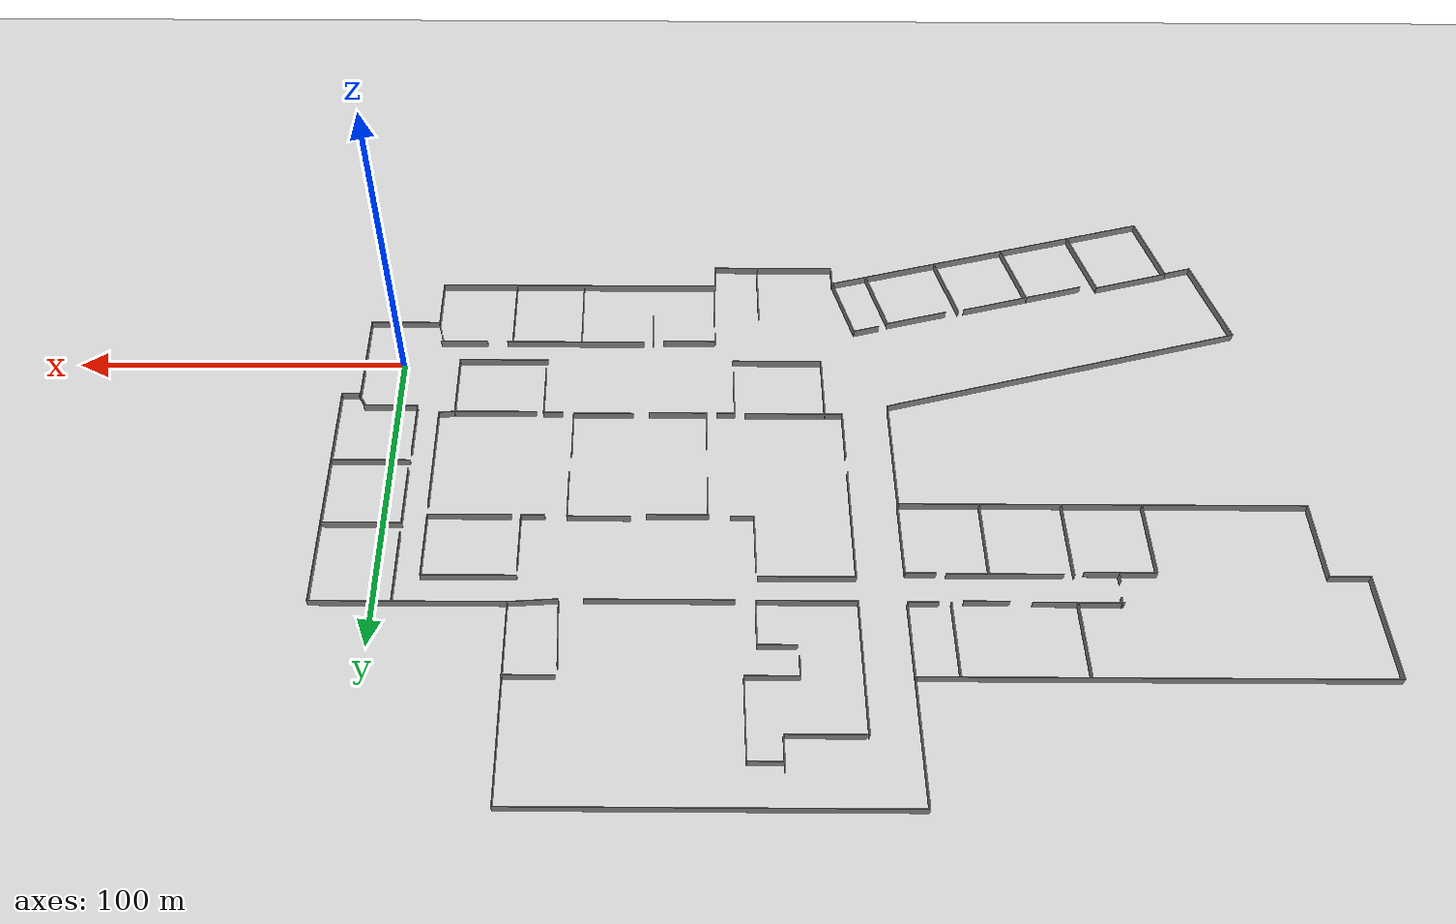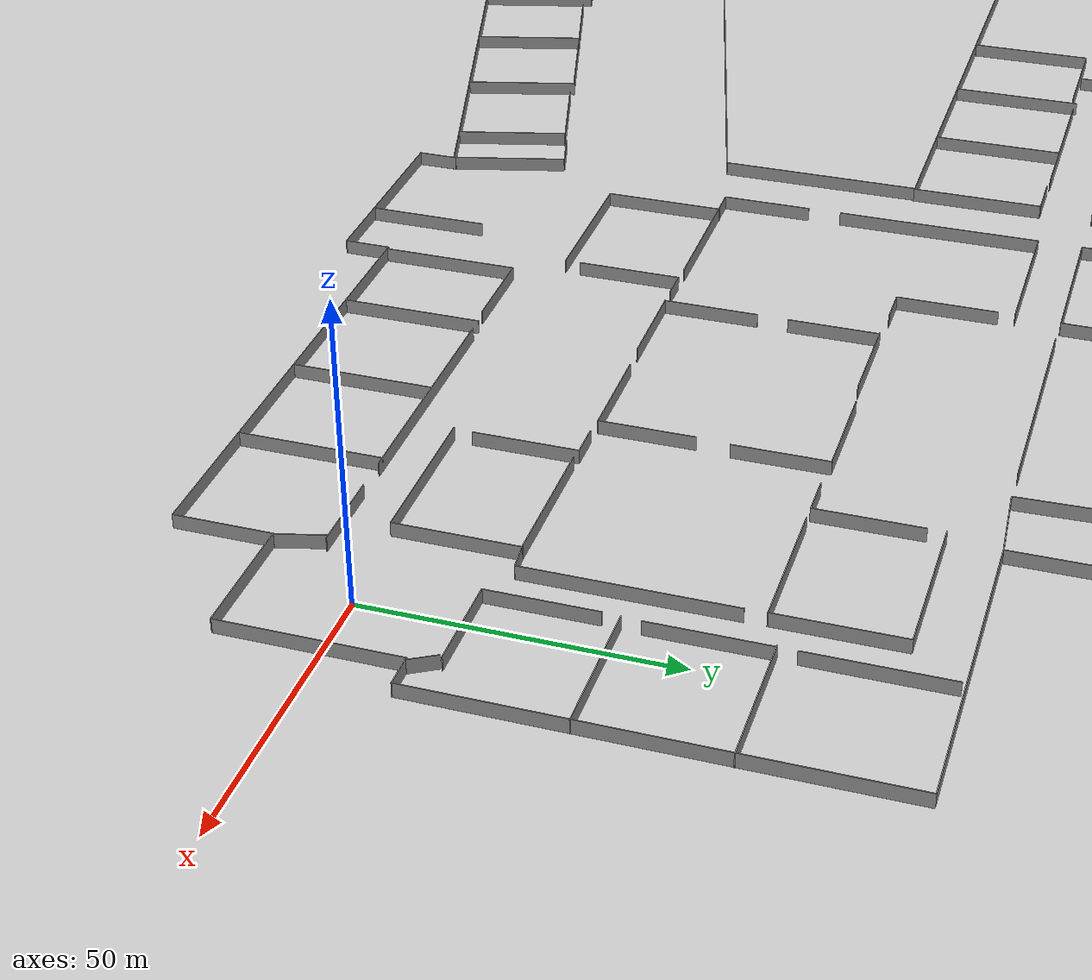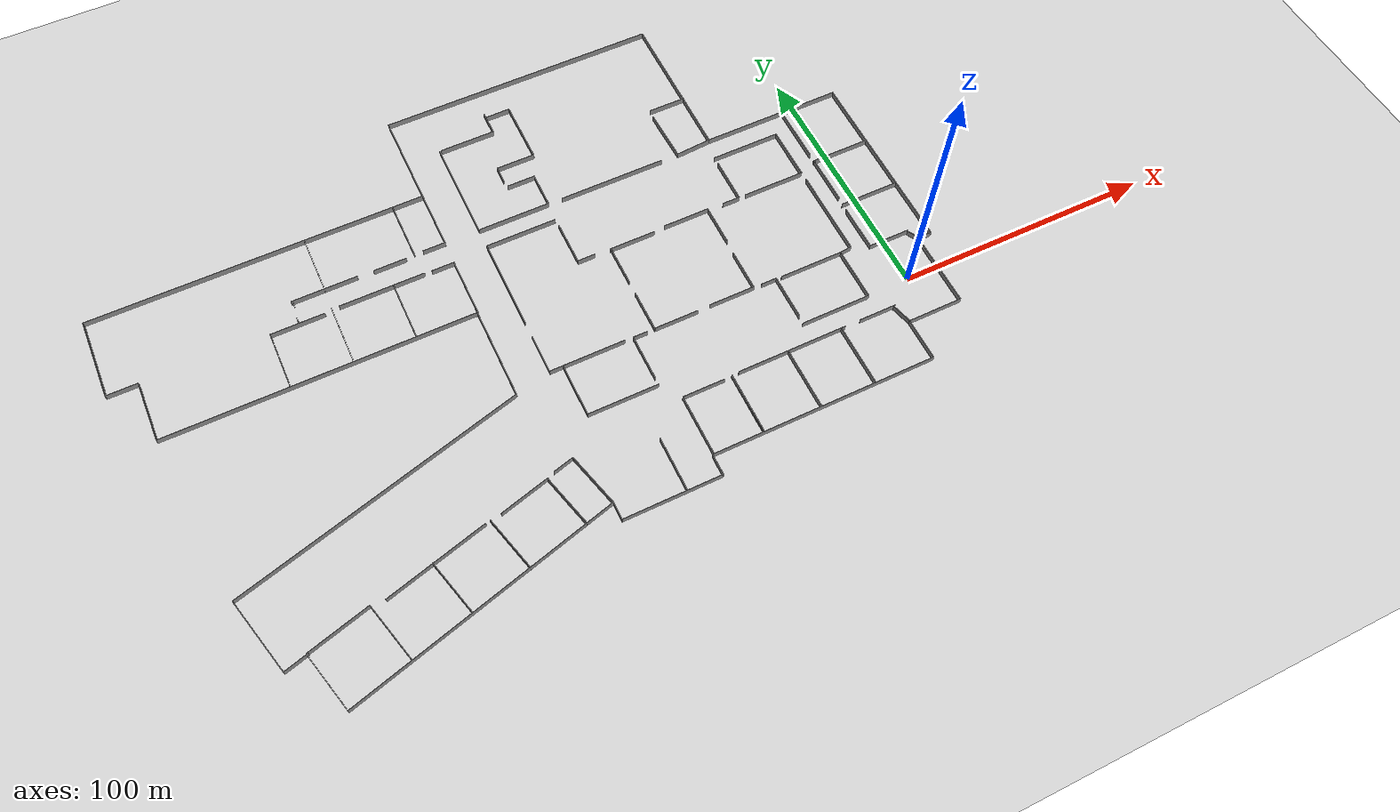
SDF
<sdf version="1.7">
 <world name="default">
  <light name="sun" type="directional">
   <pose>0 0 10 0 -0 0</pose>
   <diffuse>0.8 0.8 0.8 1</diffuse>
   <specular>0.2 0.2 0.2 1</specular>
   <attenuation>
    <range>1000</range>
    <constant>0.9</constant>
    <linear>0.01</linear>
    <quadratic>0.001</quadratic>
   </attenuation>
   <direction>-0.5 0.1 -0.9</direction>
   <spot><inner_angle>0</inner_angle><outer_angle>0</outer_angle><falloff>0</falloff></spot>
  </light>
  <model name="ground_plane">
   <static>1</static>
   <link name="link">
    <collision name="collision">
     <geometry><plane><normal>0 0 1</normal><size>100 100</size></plane></geometry>
     <surface>
      <contact><collide_bitmask>65535</collide_bitmask></contact>
      <friction><ode><mu>100</mu><mu2>50</mu2></ode></friction>
     </surface>
    </collision>
    <visual name="visual">
     <cast_shadows>0</cast_shadows>
     <geometry><plane><normal>0 0 1</normal><size>100 100</size></plane></geometry>
     <material>
      <script><uri>file://media/materials/scripts/gazebo.material</uri><name>Gazebo/Grey</name></script>
     </material>
    </visual>
   </link>
  </model>
  <gravity>0 0 -9.8</gravity>
  <magnetic_field>6e-06 2.3e-05 -4.2e-05</magnetic_field>
  <atmosphere type="adiabatic"/>
  <physics type="ode">
   <max_step_size>0.001</max_step_size>
   <real_time_factor>1</real_time_factor>
   <real_time_update_rate>1000</real_time_update_rate>
  </physics>
  <scene><ambient>0.4 0.4 0.4 1</ambient><background>0.7 0.7 0.7 1</background><shadows>1</shadows></scene>
  <audio><device>default</device></audio>
  <spherical_coordinates>
   <surface_model>EARTH_WGS84</surface_model>
   <latitude_deg>0</latitude_deg>
   <longitude_deg>0</longitude_deg>
   <elevation>0</elevation>
   <heading_deg>0</heading_deg>
  </spherical_coordinates>
  <model name="DohertyFinal">
   <pose>-129.277 42.9973 0 0 -0 0</pose>
   <link name="Wall_0">
    <collision name="Wall_0_Collision">
     <geometry><box><size>11.75 0.15 2.5</size></box></geometry>
     <pose>0 0 1.25 0 -0 0</pose>
    </collision>
    <visual name="Wall_0_Visual">
     <pose>0 0 1.25 0 -0 0</pose>
     <geometry><box><size>11.75 0.15 2.5</size></box></geometry>
     <material>
      <script><uri>file://media/materials/scripts/gazebo.material</uri><name>Gazebo/Grey</name></script>
      <ambient>1 1 1 1</ambient>
     </material>
     <meta><layer>0</layer></meta>
    </visual>
    <pose>-141.015 34.4358 0 0 -0 3.14159</pose>
   </link>
   <link name="Wall_1">
    <collision name="Wall_1_Collision">
     <geometry><box><size>32.5 0.15 2.5</size></box></geometry>
     <pose>0 0 1.25 0 -0 0</pose>
    </collision>
    <visual name="Wall_1_Visual">
     <pose>0 0 1.25 0 -0 0</pose>
     <geometry><box><size>32.5 0.15 2.5</size></box></geometry>
     <material>
      <script><uri>file://media/materials/scripts/gazebo.material</uri><name>Gazebo/Grey</name></script>
      <ambient>1 1 1 1</ambient>
     </material>
     <meta><layer>0</layer></meta>
    </visual>
    <pose>-146.815 50.6108 0 0 -0 1.5708</pose>
   </link>
   <link name="Wall_10">
    <collision name="Wall_10_Collision">
     <geometry><box><size>25.25 0.15 2.5</size></box></geometry>
     <pose>0 0 1.25 0 -0 0</pose>
    </collision>
    <visual name="Wall_10_Visual">
     <pose>0 0 1.25 0 -0 0</pose>
     <geometry><box><size>25.25 0.15 2.5</size></box></geometry>
     <material>
      <script><uri>file://media/materials/scripts/gazebo.material</uri><name>Gazebo/Grey</name></script>
      <ambient>1 1 1 1</ambient>
     </material>
     <meta><layer>0</layer></meta>
    </visual>
    <pose>-64.5141 43.3806 0 0 -0 3.14159</pose>
   </link>
   <link name="Wall_100">
    <collision name="Wall_100_Collision">
     <geometry><box><size>28.25 0.15 2.5</size></box></geometry>
     <pose>0 0 1.25 0 -0 0</pose>
    </collision>
    <visual name="Wall_100_Visual">
     <pose>0 0 1.25 0 -0 0</pose>
     <geometry><box><size>28.25 0.15 2.5</size></box></geometry>
     <material>
      <script><uri>file://media/materials/scripts/gazebo.material</uri><name>Gazebo/Grey</name></script>
      <ambient>1 1 1 1</ambient>
     </material>
     <meta><layer>0</layer></meta>
    </visual>
    <pose>9.77862 43.2354 0 0 -0 0</pose>
   </link>
   <link name="Wall_102">
    <collision name="Wall_102_Collision">
     <geometry><box><size>41.75 0.15 2.5</size></box></geometry>
     <pose>0 0 1.25 0 -0 0</pose>
    </collision>
    <visual name="Wall_102_Visual">
     <pose>0 0 1.25 0 -0 0</pose>
     <geometry><box><size>41.75 0.15 2.5</size></box></geometry>
     <material>
      <script><uri>file://media/materials/scripts/gazebo.material</uri><name>Gazebo/Grey</name></script>
      <ambient>1 1 1 1</ambient>
     </material>
     <meta><layer>0</layer></meta>
    </visual>
    <pose>50.228 43.0752 0 0 -0 0</pose>
   </link>
   <link name="Wall_104">
    <collision name="Wall_104_Collision">
     <geometry><box><size>14.1764 0.15 2.5</size></box></geometry>
     <pose>0 0 1.25 0 -0 0</pose>
    </collision>
    <visual name="Wall_104_Visual">
     <pose>0 0 1.25 0 -0 0</pose>
     <geometry><box><size>14.1764 0.15 2.5</size></box></geometry>
     <material>
      <script><uri>file://media/materials/scripts/gazebo.material</uri><name>Gazebo/Grey</name></script>
      <ambient>1 1 1 1</ambient>
     </material>
     <meta><layer>0</layer></meta>
    </visual>
    <pose>84.8878 43.5555 0 0 -0 0.068536</pose>
   </link>
   <link name="Wall_106">
    <collision name="Wall_106_Collision">
     <geometry><box><size>21.75 0.15 2.5</size></box></geometry>
     <pose>0 0 1.25 0 -0 0</pose>
    </collision>
    <visual name="Wall_106_Visual">
     <pose>0 0 1.25 0 -0 0</pose>
     <geometry><box><size>21.75 0.15 2.5</size></box></geometry>
     <material>
      <script><uri>file://media/materials/scripts/gazebo.material</uri><name>Gazebo/Grey</name></script>
      <ambient>1 1 1 1</ambient>
     </material>
     <meta><layer>0</layer></meta>
    </visual>
    <pose>7.17052 83.8354 0 0 -0 0</pose>
   </link>
   <link name="Wall_107">
    <collision name="Wall_107_Collision">
     <geometry><box><size>10 0.15 2.5</size></box></geometry>
     <pose>0 0 1.25 0 -0 0</pose>
    </collision>
    <visual name="Wall_107_Visual">
     <pose>0 0 1.25 0 -0 0</pose>
     <geometry><box><size>10 0.15 2.5</size></box></geometry>
     <material>
      <script><uri>file://media/materials/scripts/gazebo.material</uri><name>Gazebo/Grey</name></script>
      <ambient>1 1 1 1</ambient>
     </material>
     <meta><layer>0</layer></meta>
    </visual>
    <pose>17.9705 88.7604 0 0 -0 1.5708</pose>
   </link>
   <link name="Wall_109">
    <collision name="Wall_109_Collision">
     <geometry><box><size>10 0.15 2.5</size></box></geometry>
     <pose>0 0 1.25 0 -0 0</pose>
    </collision>
    <visual name="Wall_109_Visual">
     <pose>0 0 1.25 0 -0 0</pose>
     <geometry><box><size>10 0.15 2.5</size></box></geometry>
     <material>
      <script><uri>file://media/materials/scripts/gazebo.material</uri><name>Gazebo/Grey</name></script>
      <ambient>1 1 1 1</ambient>
     </material>
     <meta><layer>0</layer></meta>
    </visual>
    <pose>22.799 91.5382 0 0 -0 0</pose>
   </link>
   <link name="Wall_110">
    <collision name="Wall_110_Collision">
     <geometry><box><size>25 0.15 2.5</size></box></geometry>
     <pose>0 0 1.25 0 -0 0</pose>
    </collision>
    <visual name="Wall_110_Visual">
     <pose>0 0 1.25 0 -0 0</pose>
     <geometry><box><size>25 0.15 2.5</size></box></geometry>
     <material>
      <script><uri>file://media/materials/scripts/gazebo.material</uri><name>Gazebo/Grey</name></script>
      <ambient>1 1 1 1</ambient>
     </material>
     <meta><layer>0</layer></meta>
    </visual>
    <pose>27.724 79.1132 0 0 -0 -1.5708</pose>
   </link>
   <link name="Wall_111">
    <collision name="Wall_111_Collision">
     <geometry><box><size>15.25 0.15 2.5</size></box></geometry>
     <pose>0 0 1.25 0 -0 0</pose>
    </collision>
    <visual name="Wall_111_Visual">
     <pose>0 0 1.25 0 -0 0</pose>
     <geometry><box><size>15.25 0.15 2.5</size></box></geometry>
     <material>
      <script><uri>file://media/materials/scripts/gazebo.material</uri><name>Gazebo/Grey</name></script>
      <ambient>1 1 1 1</ambient>
     </material>
     <meta><layer>0</layer></meta>
    </visual>
    <pose>20.174 66.6882 0 0 -0 3.14159</pose>
   </link>
   <link name="Wall_112">
    <collision name="Wall_112_Collision">
     <geometry><box><size>6.5 0.15 2.5</size></box></geometry>
     <pose>0 0 1.25 0 -0 0</pose>
    </collision>
    <visual name="Wall_112_Visual">
     <pose>0 0 1.25 0 -0 0</pose>
     <geometry><box><size>6.5 0.15 2.5</size></box></geometry>
     <material>
      <script><uri>file://media/materials/scripts/gazebo.material</uri><name>Gazebo/Grey</name></script>
      <ambient>1 1 1 1</ambient>
     </material>
     <meta><layer>0</layer></meta>
    </visual>
    <pose>12.624 63.5132 0 0 -0 -1.5708</pose>
   </link>
   <link name="Wall_114">
    <collision name="Wall_114_Collision">
     <geometry><box><size>11 0.15 2.5</size></box></geometry>
     <pose>0 0 1.25 0 -0 0</pose>
    </collision>
    <visual name="Wall_114_Visual">
     <pose>0 0 1.25 0 -0 0</pose>
     <geometry><box><size>11 0.15 2.5</size></box></geometry>
     <material>
      <script><uri>file://media/materials/scripts/gazebo.material</uri><name>Gazebo/Grey</name></script>
      <ambient>1 1 1 1</ambient>
     </material>
     <meta><layer>0</layer></meta>
    </visual>
    <pose>18.4848 57.1969 0 0 -0 0</pose>
   </link>
   <link name="Wall_115">
    <collision name="Wall_115_Collision">
     <geometry><box><size>14.1116 0.15 2.5</size></box></geometry>
     <pose>0 0 1.25 0 -0 0</pose>
    </collision>
    <visual name="Wall_115_Visual">
     <pose>0 0 1.25 0 -0 0</pose>
     <geometry><box><size>14.1116 0.15 2.5</size></box></geometry>
     <material>
      <script><uri>file://media/materials/scripts/gazebo.material</uri><name>Gazebo/Grey</name></script>
      <ambient>1 1 1 1</ambient>
     </material>
     <meta><layer>0</layer></meta>
    </visual>
    <pose>23.8692 50.2161 0 0 -0 -1.57661</pose>
   </link>
   <link name="Wall_120">
    <collision name="Wall_120_Collision">
     <geometry><box><size>14.5 0.15 2.5</size></box></geometry>
     <pose>0 0 1.25 0 -0 0</pose>
    </collision>
    <visual name="Wall_120_Visual">
     <pose>0 0 1.25 0 -0 0</pose>
     <geometry><box><size>14.5 0.15 2.5</size></box></geometry>
     <material>
      <script><uri>file://media/materials/scripts/gazebo.material</uri><name>Gazebo/Grey</name></script>
      <ambient>1 1 1 1</ambient>
     </material>
     <meta><layer>0</layer></meta>
    </visual>
    <pose>84.8377 66.8253 0 0 -0 3.14159</pose>
   </link>
   <link name="Wall_122">
    <collision name="Wall_122_Collision">
     <geometry><box><size>21.0214 0.15 2.5</size></box></geometry>
     <pose>0 0 1.25 0 -0 0</pose>
    </collision>
    <visual name="Wall_122_Visual">
     <pose>0 0 1.25 0 -0 0</pose>
     <geometry><box><size>21.0214 0.15 2.5</size></box></geometry>
     <material>
      <script><uri>file://media/materials/scripts/gazebo.material</uri><name>Gazebo/Grey</name></script>
      <ambient>1 1 1 1</ambient>
     </material>
     <meta><layer>0</layer></meta>
    </visual>
    <pose>77.5701 53.506 0 0 -0 -1.54004</pose>
   </link>
   <link name="Wall_124">
    <collision name="Wall_124_Collision">
     <geometry><box><size>27.5 0.15 2.5</size></box></geometry>
     <pose>0 0 1.25 0 -0 0</pose>
    </collision>
    <visual name="Wall_124_Visual">
     <pose>0 0 1.25 0 -0 0</pose>
     <geometry><box><size>27.5 0.15 2.5</size></box></geometry>
     <material>
      <script><uri>file://media/materials/scripts/gazebo.material</uri><name>Gazebo/Grey</name></script>
      <ambient>1 1 1 1</ambient>
     </material>
     <meta><layer>0</layer></meta>
    </visual>
    <pose>9.33411 35.3725 0 0 -0 3.14159</pose>
   </link>
   <link name="Wall_125">
    <collision name="Wall_125_Collision">
     <geometry><box><size>36.5 0.15 2.5</size></box></geometry>
     <pose>0 0 1.25 0 -0 0</pose>
    </collision>
    <visual name="Wall_125_Visual">
     <pose>0 0 1.25 0 -0 0</pose>
     <geometry><box><size>36.5 0.15 2.5</size></box></geometry>
     <material>
      <script><uri>file://media/materials/scripts/gazebo.material</uri><name>Gazebo/Grey</name></script>
      <ambient>1 1 1 1</ambient>
     </material>
     <meta><layer>0</layer></meta>
    </visual>
    <pose>-4.34089 17.1975 0 0 -0 -1.5708</pose>
   </link>
   <link name="Wall_127">
    <collision name="Wall_127_Collision">
     <geometry><box><size>16 0.15 2.5</size></box></geometry>
     <pose>0 0 1.25 0 -0 0</pose>
    </collision>
    <visual name="Wall_127_Visual">
     <pose>0 0 1.25 0 -0 0</pose>
     <geometry><box><size>16 0.15 2.5</size></box></geometry>
     <material>
      <script><uri>file://media/materials/scripts/gazebo.material</uri><name>Gazebo/Grey</name></script>
      <ambient>1 1 1 1</ambient>
     </material>
     <meta><layer>0</layer></meta>
    </visual>
    <pose>-4.27137 -14.9175 0 0 -0 -1.5708</pose>
   </link>
   <link name="Wall_128">
    <collision name="Wall_128_Collision">
     <geometry><box><size>29.25 0.15 2.5</size></box></geometry>
     <pose>0 0 1.25 0 -0 0</pose>
    </collision>
    <visual name="Wall_128_Visual">
     <pose>0 0 1.25 0 -0 0</pose>
     <geometry><box><size>29.25 0.15 2.5</size></box></geometry>
     <material>
      <script><uri>file://media/materials/scripts/gazebo.material</uri><name>Gazebo/Grey</name></script>
      <ambient>1 1 1 1</ambient>
     </material>
     <meta><layer>0</layer></meta>
    </visual>
    <pose>10.2786 -22.8425 0 0 -0 0</pose>
   </link>
   <link name="Wall_13">
    <collision name="Wall_13_Collision">
     <geometry><box><size>23.25 0.15 2.5</size></box></geometry>
     <pose>0 0 1.25 0 -0 0</pose>
    </collision>
    <visual name="Wall_13_Visual">
     <pose>0 0 1.25 0 -0 0</pose>
     <geometry><box><size>23.25 0.15 2.5</size></box></geometry>
     <material>
      <script><uri>file://media/materials/scripts/gazebo.material</uri><name>Gazebo/Grey</name></script>
      <ambient>1 1 1 1</ambient>
     </material>
     <meta><layer>0</layer></meta>
    </visual>
    <pose>-64.4104 54.9306 0 0 -0 1.5708</pose>
   </link>
   <link name="Wall_130">
    <collision name="Wall_130_Collision">
     <geometry><box><size>17.75 0.15 2.5</size></box></geometry>
     <pose>0 0 1.25 0 -0 0</pose>
    </collision>
    <visual name="Wall_130_Visual">
     <pose>0 0 1.25 0 -0 0</pose>
     <geometry><box><size>17.75 0.15 2.5</size></box></geometry>
     <material>
      <script><uri>file://media/materials/scripts/gazebo.material</uri><name>Gazebo/Grey</name></script>
      <ambient>1 1 1 1</ambient>
     </material>
     <meta><layer>0</layer></meta>
    </visual>
    <pose>23.3301 23.6839 0 0 -0 -1.5708</pose>
   </link>
   <link name="Wall_131">
    <collision name="Wall_131_Collision">
     <geometry><box><size>6.75 0.15 2.5</size></box></geometry>
     <pose>0 0 1.25 0 -0 0</pose>
    </collision>
    <visual name="Wall_131_Visual">
     <pose>0 0 1.25 0 -0 0</pose>
     <geometry><box><size>6.75 0.15 2.5</size></box></geometry>
     <material>
      <script><uri>file://media/materials/scripts/gazebo.material</uri><name>Gazebo/Grey</name></script>
      <ambient>1 1 1 1</ambient>
     </material>
     <meta><layer>0</layer></meta>
    </visual>
    <pose>26.6301 14.8839 0 0 -0 0</pose>
   </link>
   <link name="Wall_133">
    <collision name="Wall_133_Collision">
     <geometry><box><size>18 0.15 2.5</size></box></geometry>
     <pose>0 0 1.25 0 -0 0</pose>
    </collision>
    <visual name="Wall_133_Visual">
     <pose>0 0 1.25 0 -0 0</pose>
     <geometry><box><size>18 0.15 2.5</size></box></geometry>
     <material>
      <script><uri>file://media/materials/scripts/gazebo.material</uri><name>Gazebo/Grey</name></script>
      <ambient>1 1 1 1</ambient>
     </material>
     <meta><layer>0</layer></meta>
    </visual>
    <pose>45.0929 14.5109 0 0 -0 0</pose>
   </link>
   <link name="Wall_135">
    <collision name="Wall_135_Collision">
     <geometry><box><size>18.25 0.15 2.5</size></box></geometry>
     <pose>0 0 1.25 0 -0 0</pose>
    </collision>
    <visual name="Wall_135_Visual">
     <pose>0 0 1.25 0 -0 0</pose>
     <geometry><box><size>18.25 0.15 2.5</size></box></geometry>
     <material>
      <script><uri>file://media/materials/scripts/gazebo.material</uri><name>Gazebo/Grey</name></script>
      <ambient>1 1 1 1</ambient>
     </material>
     <meta><layer>0</layer></meta>
    </visual>
    <pose>67.6842 15.1528 0 0 -0 0</pose>
   </link>
   <link name="Wall_136">
    <collision name="Wall_136_Collision">
     <geometry><box><size>16.25 0.15 2.5</size></box></geometry>
     <pose>0 0 1.25 0 -0 0</pose>
    </collision>
    <visual name="Wall_136_Visual">
     <pose>0 0 1.25 0 -0 0</pose>
     <geometry><box><size>16.25 0.15 2.5</size></box></geometry>
     <material>
      <script><uri>file://media/materials/scripts/gazebo.material</uri><name>Gazebo/Grey</name></script>
      <ambient>1 1 1 1</ambient>
     </material>
     <meta><layer>0</layer></meta>
    </visual>
    <pose>76.7342 7.10281 0 0 -0 -1.5708</pose>
   </link>
   <link name="Wall_138">
    <collision name="Wall_138_Collision">
     <geometry><box><size>16.25 0.15 2.5</size></box></geometry>
     <pose>0 0 1.25 0 -0 0</pose>
    </collision>
    <visual name="Wall_138_Visual">
     <pose>0 0 1.25 0 -0 0</pose>
     <geometry><box><size>16.25 0.15 2.5</size></box></geometry>
     <material>
      <script><uri>file://media/materials/scripts/gazebo.material</uri><name>Gazebo/Grey</name></script>
      <ambient>1 1 1 1</ambient>
     </material>
     <meta><layer>0</layer></meta>
    </visual>
    <pose>76.2863 -14.7216 0 0 -0 -1.5708</pose>
   </link>
   <link name="Wall_139">
    <collision name="Wall_139_Collision">
     <geometry><box><size>18 0.15 2.5</size></box></geometry>
     <pose>0 0 1.25 0 -0 0</pose>
    </collision>
    <visual name="Wall_139_Visual">
     <pose>0 0 1.25 0 -0 0</pose>
     <geometry><box><size>18 0.15 2.5</size></box></geometry>
     <material>
      <script><uri>file://media/materials/scripts/gazebo.material</uri><name>Gazebo/Grey</name></script>
      <ambient>1 1 1 1</ambient>
     </material>
     <meta><layer>0</layer></meta>
    </visual>
    <pose>67.3613 -22.7716 0 0 -0 3.14159</pose>
   </link>
   <link name="Wall_141">
    <collision name="Wall_141_Collision">
     <geometry><box><size>17.25 0.15 2.5</size></box></geometry>
     <pose>0 0 1.25 0 -0 0</pose>
    </collision>
    <visual name="Wall_141_Visual">
     <pose>0 0 1.25 0 -0 0</pose>
     <geometry><box><size>17.25 0.15 2.5</size></box></geometry>
     <material>
      <script><uri>file://media/materials/scripts/gazebo.material</uri><name>Gazebo/Grey</name></script>
      <ambient>1 1 1 1</ambient>
     </material>
     <meta><layer>0</layer></meta>
    </visual>
    <pose>44.9491 -23.0399 0 0 -0 3.14159</pose>
   </link>
   <link name="Wall_142">
    <collision name="Wall_142_Collision">
     <geometry><box><size>16.5 0.15 2.5</size></box></geometry>
     <pose>0 0 1.25 0 -0 0</pose>
    </collision>
    <visual name="Wall_142_Visual">
     <pose>0 0 1.25 0 -0 0</pose>
     <geometry><box><size>16.5 0.15 2.5</size></box></geometry>
     <material>
      <script><uri>file://media/materials/scripts/gazebo.material</uri><name>Gazebo/Grey</name></script>
      <ambient>1 1 1 1</ambient>
     </material>
     <meta><layer>0</layer></meta>
    </visual>
    <pose>36.3991 -14.8649 0 0 -0 1.5708</pose>
   </link>
   <link name="Wall_144">
    <collision name="Wall_144_Collision">
     <geometry><box><size>15.75 0.15 2.5</size></box></geometry>
     <pose>0 0 1.25 0 -0 0</pose>
    </collision>
    <visual name="Wall_144_Visual">
     <pose>0 0 1.25 0 -0 0</pose>
     <geometry><box><size>15.75 0.15 2.5</size></box></geometry>
     <material>
      <script><uri>file://media/materials/scripts/gazebo.material</uri><name>Gazebo/Grey</name></script>
      <ambient>1 1 1 1</ambient>
     </material>
     <meta><layer>0</layer></meta>
    </visual>
    <pose>36.4889 6.58453 0 0 -0 1.5708</pose>
   </link>
   <link name="Wall_146">
    <collision name="Wall_146_Collision">
     <geometry><box><size>21.25 0.15 2.5</size></box></geometry>
     <pose>0 0 1.25 0 -0 0</pose>
    </collision>
    <visual name="Wall_146_Visual">
     <pose>0 0 1.25 0 -0 0</pose>
     <geometry><box><size>21.25 0.15 2.5</size></box></geometry>
     <material>
      <script><uri>file://media/materials/scripts/gazebo.material</uri><name>Gazebo/Grey</name></script>
      <ambient>1 1 1 1</ambient>
     </material>
     <meta><layer>0</layer></meta>
    </visual>
    <pose>0.863775 -33.2778 0 0 -0 -1.5708</pose>
   </link>
   <link name="Wall_147">
    <collision name="Wall_147_Collision">
     <geometry><box><size>27.25 0.15 2.5</size></box></geometry>
     <pose>0 0 1.25 0 -0 0</pose>
    </collision>
    <visual name="Wall_147_Visual">
     <pose>0 0 1.25 0 -0 0</pose>
     <geometry><box><size>27.25 0.15 2.5</size></box></geometry>
     <material>
      <script><uri>file://media/materials/scripts/gazebo.material</uri><name>Gazebo/Grey</name></script>
      <ambient>1 1 1 1</ambient>
     </material>
     <meta><layer>0</layer></meta>
    </visual>
    <pose>14.4138 -43.8278 0 0 -0 0</pose>
   </link>
   <link name="Wall_151">
    <collision name="Wall_151_Collision">
     <geometry><box><size>5.5 0.15 2.5</size></box></geometry>
     <pose>0 0 1.25 0 -0 0</pose>
    </collision>
    <visual name="Wall_151_Visual">
     <pose>0 0 1.25 0 -0 0</pose>
     <geometry><box><size>5.5 0.15 2.5</size></box></geometry>
     <material>
      <script><uri>file://media/materials/scripts/gazebo.material</uri><name>Gazebo/Grey</name></script>
      <ambient>1 1 1 1</ambient>
     </material>
     <meta><layer>0</layer></meta>
    </visual>
    <pose>30.6044 -23.0488 0 0 -0 3.14159</pose>
   </link>
   <link name="Wall_152">
    <collision name="Wall_152_Collision">
     <geometry><box><size>18.25 0.15 2.5</size></box></geometry>
     <pose>0 0 1.25 0 -0 0</pose>
    </collision>
    <visual name="Wall_152_Visual">
     <pose>0 0 1.25 0 -0 0</pose>
     <geometry><box><size>18.25 0.15 2.5</size></box></geometry>
     <material>
      <script><uri>file://media/materials/scripts/gazebo.material</uri><name>Gazebo/Grey</name></script>
      <ambient>1 1 1 1</ambient>
     </material>
     <meta><layer>0</layer></meta>
    </visual>
    <pose>27.9294 -32.0988 0 0 -0 -1.5708</pose>
   </link>
   <link name="Wall_154">
    <collision name="Wall_154_Collision">
     <geometry><box><size>6 0.15 2.5</size></box></geometry>
     <pose>0 0 1.25 0 -0 0</pose>
    </collision>
    <visual name="Wall_154_Visual">
     <pose>0 0 1.25 0 -0 0</pose>
     <geometry><box><size>6 0.15 2.5</size></box></geometry>
     <material>
      <script><uri>file://media/materials/scripts/gazebo.material</uri><name>Gazebo/Grey</name></script>
      <ambient>1 1 1 1</ambient>
     </material>
     <meta><layer>0</layer></meta>
    </visual>
    <pose>82.4208 -23.0488 0 0 -0 0</pose>
   </link>
   <link name="Wall_155">
    <collision name="Wall_155_Collision">
     <geometry><box><size>17.75 0.15 2.5</size></box></geometry>
     <pose>0 0 1.25 0 -0 0</pose>
    </collision>
    <visual name="Wall_155_Visual">
     <pose>0 0 1.25 0 -0 0</pose>
     <geometry><box><size>17.75 0.15 2.5</size></box></geometry>
     <material>
      <script><uri>file://media/materials/scripts/gazebo.material</uri><name>Gazebo/Grey</name></script>
      <ambient>1 1 1 1</ambient>
     </material>
     <meta><layer>0</layer></meta>
    </visual>
    <pose>85.3458 -31.8488 0 0 -0 -1.5708</pose>
   </link>
   <link name="Wall_157">
    <collision name="Wall_157_Collision">
     <geometry><box><size>27.25 0.15 2.5</size></box></geometry>
     <pose>0 0 1.25 0 -0 0</pose>
    </collision>
    <visual name="Wall_157_Visual">
     <pose>0 0 1.25 0 -0 0</pose>
     <geometry><box><size>27.25 0.15 2.5</size></box></geometry>
     <material>
      <script><uri>file://media/materials/scripts/gazebo.material</uri><name>Gazebo/Grey</name></script>
      <ambient>1 1 1 1</ambient>
     </material>
     <meta><layer>0</layer></meta>
    </visual>
    <pose>98.5019 -43.9103 0 0 -0 0</pose>
   </link>
   <link name="Wall_158">
    <collision name="Wall_158_Collision">
     <geometry><box><size>20.75 0.15 2.5</size></box></geometry>
     <pose>0 0 1.25 0 -0 0</pose>
    </collision>
    <visual name="Wall_158_Visual">
     <pose>0 0 1.25 0 -0 0</pose>
     <geometry><box><size>20.75 0.15 2.5</size></box></geometry>
     <material>
      <script><uri>file://media/materials/scripts/gazebo.material</uri><name>Gazebo/Grey</name></script>
      <ambient>1 1 1 1</ambient>
     </material>
     <meta><layer>0</layer></meta>
    </visual>
    <pose>112.052 -33.6103 0 0 -0 1.5708</pose>
   </link>
   <link name="Wall_159">
    <collision name="Wall_159_Collision">
     <geometry><box><size>24.75 0.15 2.5</size></box></geometry>
     <pose>0 0 1.25 0 -0 0</pose>
    </collision>
    <visual name="Wall_159_Visual">
     <pose>0 0 1.25 0 -0 0</pose>
     <geometry><box><size>24.75 0.15 2.5</size></box></geometry>
     <material>
      <script><uri>file://media/materials/scripts/gazebo.material</uri><name>Gazebo/Grey</name></script>
      <ambient>1 1 1 1</ambient>
     </material>
     <meta><layer>0</layer></meta>
    </visual>
    <pose>99.7519 -23.3103 0 0 -0 3.14159</pose>
   </link>
   <link name="Wall_161">
    <collision name="Wall_161_Collision">
     <geometry><box><size>7 0.15 2.5</size></box></geometry>
     <pose>0 0 1.25 0 -0 0</pose>
    </collision>
    <visual name="Wall_161_Visual">
     <pose>0 0 1.25 0 -0 0</pose>
     <geometry><box><size>7 0.15 2.5</size></box></geometry>
     <material>
      <script><uri>file://media/materials/scripts/gazebo.material</uri><name>Gazebo/Grey</name></script>
      <ambient>1 1 1 1</ambient>
     </material>
     <meta><layer>0</layer></meta>
    </visual>
    <pose>86.4512 14.823 0 0 -0 0</pose>
   </link>
   <link name="Wall_162">
    <collision name="Wall_162_Collision">
     <geometry><box><size>17.75 0.15 2.5</size></box></geometry>
     <pose>0 0 1.25 0 -0 0</pose>
    </collision>
    <visual name="Wall_162_Visual">
     <pose>0 0 1.25 0 -0 0</pose>
     <geometry><box><size>17.75 0.15 2.5</size></box></geometry>
     <material>
      <script><uri>file://media/materials/scripts/gazebo.material</uri><name>Gazebo/Grey</name></script>
      <ambient>1 1 1 1</ambient>
     </material>
     <meta><layer>0</layer></meta>
    </visual>
    <pose>89.8762 23.623 0 0 -0 1.5708</pose>
   </link>
   <link name="Wall_164">
    <collision name="Wall_164_Collision">
     <geometry><box><size>27 0.15 2.5</size></box></geometry>
     <pose>0 0 1.25 0 -0 0</pose>
    </collision>
    <visual name="Wall_164_Visual">
     <pose>0 0 1.25 0 -0 0</pose>
     <geometry><box><size>27 0.15 2.5</size></box></geometry>
     <material>
      <script><uri>file://media/materials/scripts/gazebo.material</uri><name>Gazebo/Grey</name></script>
      <ambient>1 1 1 1</ambient>
     </material>
     <meta><layer>0</layer></meta>
    </visual>
    <pose>103.191 35.3636 0 0 -0 0</pose>
   </link>
   <link name="Wall_165">
    <collision name="Wall_165_Collision">
     <geometry><box><size>20.75 0.15 2.5</size></box></geometry>
     <pose>0 0 1.25 0 -0 0</pose>
    </collision>
    <visual name="Wall_165_Visual">
     <pose>0 0 1.25 0 -0 0</pose>
     <geometry><box><size>20.75 0.15 2.5</size></box></geometry>
     <material>
      <script><uri>file://media/materials/scripts/gazebo.material</uri><name>Gazebo/Grey</name></script>
      <ambient>1 1 1 1</ambient>
     </material>
     <meta><layer>0</layer></meta>
    </visual>
    <pose>116.616 25.0636 0 0 -0 -1.5708</pose>
   </link>
   <link name="Wall_166">
    <collision name="Wall_166_Collision">
     <geometry><box><size>24.25 0.15 2.5</size></box></geometry>
     <pose>0 0 1.25 0 -0 0</pose>
    </collision>
    <visual name="Wall_166_Visual">
     <pose>0 0 1.25 0 -0 0</pose>
     <geometry><box><size>24.25 0.15 2.5</size></box></geometry>
     <material>
      <script><uri>file://media/materials/scripts/gazebo.material</uri><name>Gazebo/Grey</name></script>
      <ambient>1 1 1 1</ambient>
     </material>
     <meta><layer>0</layer></meta>
    </visual>
    <pose>104.566 14.7636 0 0 -0 3.14159</pose>
   </link>
   <link name="Wall_168">
    <collision name="Wall_168_Collision">
     <geometry><box><size>34.25 0.15 2.5</size></box></geometry>
     <pose>0 0 1.25 0 -0 0</pose>
    </collision>
    <visual name="Wall_168_Visual">
     <pose>0 0 1.25 0 -0 0</pose>
     <geometry><box><size>34.25 0.15 2.5</size></box></geometry>
     <material>
      <script><uri>file://media/materials/scripts/gazebo.material</uri><name>Gazebo/Grey</name></script>
      <ambient>1 1 1 1</ambient>
     </material>
     <meta><layer>0</layer></meta>
    </visual>
    <pose>116.726 -5.7575 0 0 -0 -1.57079</pose>
   </link>
   <link name="Wall_17">
    <collision name="Wall_17_Collision">
     <geometry><box><size>24 0.15 2.5</size></box></geometry>
     <pose>0 0 1.25 0 -0 0</pose>
    </collision>
    <visual name="Wall_17_Visual">
     <pose>0 0 1.25 0 -0 0</pose>
     <geometry><box><size>24 0.15 2.5</size></box></geometry>
     <material>
      <script><uri>file://media/materials/scripts/gazebo.material</uri><name>Gazebo/Grey</name></script>
      <ambient>1 1 1 1</ambient>
     </material>
     <meta><layer>0</layer></meta>
    </visual>
    <pose>-135.258 22.2007 0 0 -0 -1.5708</pose>
   </link>
   <link name="Wall_172">
    <collision name="Wall_172_Collision">
     <geometry><box><size>4.85103 0.15 2.5</size></box></geometry>
     <pose>0 0 1.25 0 -0 0</pose>
    </collision>
    <visual name="Wall_172_Visual">
     <pose>0 0 1.25 0 -0 0</pose>
     <geometry><box><size>4.85103 0.15 2.5</size></box></geometry>
     <material>
      <script><uri>file://media/materials/scripts/gazebo.material</uri><name>Gazebo/Grey</name></script>
      <ambient>1 1 1 1</ambient>
     </material>
     <meta><layer>0</layer></meta>
    </visual>
    <pose>114.389 -23.0589 0 0 -0 -3.03444</pose>
   </link>
   <link name="Wall_174">
    <collision name="Wall_174_Collision">
     <geometry><box><size>21 0.15 2.5</size></box></geometry>
     <pose>0 0 1.25 0 -0 0</pose>
    </collision>
    <visual name="Wall_174_Visual">
     <pose>0 0 1.25 0 -0 0</pose>
     <geometry><box><size>21 0.15 2.5</size></box></geometry>
     <material>
      <script><uri>file://media/materials/scripts/gazebo.material</uri><name>Gazebo/Grey</name></script>
      <ambient>1 1 1 1</ambient>
     </material>
     <meta><layer>0</layer></meta>
    </visual>
    <pose>19.3349 -73.171 0 0 -0 1.5708</pose>
   </link>
   <link name="Wall_176">
    <collision name="Wall_176_Collision">
     <geometry><box><size>24 0.15 2.5</size></box></geometry>
     <pose>0 0 1.25 0 -0 0</pose>
    </collision>
    <visual name="Wall_176_Visual">
     <pose>0 0 1.25 0 -0 0</pose>
     <geometry><box><size>24 0.15 2.5</size></box></geometry>
     <material>
      <script><uri>file://media/materials/scripts/gazebo.material</uri><name>Gazebo/Grey</name></script>
      <ambient>1 1 1 1</ambient>
     </material>
     <meta><layer>0</layer></meta>
    </visual>
    <pose>33.2891 -63.8566 0 0 -0 1.5708</pose>
   </link>
   <link name="Wall_177">
    <collision name="Wall_177_Collision">
     <geometry><box><size>16.25 0.15 2.5</size></box></geometry>
     <pose>0 0 1.25 0 -0 0</pose>
    </collision>
    <visual name="Wall_177_Visual">
     <pose>0 0 1.25 0 -0 0</pose>
     <geometry><box><size>16.25 0.15 2.5</size></box></geometry>
     <material>
      <script><uri>file://media/materials/scripts/gazebo.material</uri><name>Gazebo/Grey</name></script>
      <ambient>1 1 1 1</ambient>
     </material>
     <meta><layer>0</layer></meta>
    </visual>
    <pose>41.3391 -51.9316 0 0 -0 0</pose>
   </link>
   <link name="Wall_179">
    <collision name="Wall_179_Collision">
     <geometry><box><size>24.25 0.15 2.5</size></box></geometry>
     <pose>0 0 1.25 0 -0 0</pose>
    </collision>
    <visual name="Wall_179_Visual">
     <pose>0 0 1.25 0 -0 0</pose>
     <geometry><box><size>24.25 0.15 2.5</size></box></geometry>
     <material>
      <script><uri>file://media/materials/scripts/gazebo.material</uri><name>Gazebo/Grey</name></script>
      <ambient>1 1 1 1</ambient>
     </material>
     <meta><layer>0</layer></meta>
    </visual>
    <pose>52.5459 -63.5513 0 0 -0 -1.5708</pose>
   </link>
   <link name="Wall_18">
    <collision name="Wall_18_Collision">
     <geometry><box><size>117.5 0.15 2.5</size></box></geometry>
     <pose>0 0 1.25 0 -0 0</pose>
    </collision>
    <visual name="Wall_18_Visual">
     <pose>0 0 1.25 0 -0 0</pose>
     <geometry><box><size>117.5 0.15 2.5</size></box></geometry>
     <material>
      <script><uri>file://media/materials/scripts/gazebo.material</uri><name>Gazebo/Grey</name></script>
      <ambient>1 1 1 1</ambient>
     </material>
     <meta><layer>0</layer></meta>
    </visual>
    <pose>-76.5833 10.2757 0 0 -0 0</pose>
   </link>
   <link name="Wall_181">
    <collision name="Wall_181_Collision">
     <geometry><box><size>42.75 0.15 2.5</size></box></geometry>
     <pose>0 0 1.25 0 -0 0</pose>
    </collision>
    <visual name="Wall_181_Visual">
     <pose>0 0 1.25 0 -0 0</pose>
     <geometry><box><size>42.75 0.15 2.5</size></box></geometry>
     <material>
      <script><uri>file://media/materials/scripts/gazebo.material</uri><name>Gazebo/Grey</name></script>
      <ambient>1 1 1 1</ambient>
     </material>
     <meta><layer>0</layer></meta>
    </visual>
    <pose>76.6367 -51.5013 0 0 -0 0</pose>
   </link>
   <link name="Wall_183">
    <collision name="Wall_183_Collision">
     <geometry><box><size>14.4709 0.15 2.5</size></box></geometry>
     <pose>0 0 1.25 0 -0 0</pose>
    </collision>
    <visual name="Wall_183_Visual">
     <pose>0 0 1.25 0 -0 0</pose>
     <geometry><box><size>14.4709 0.15 2.5</size></box></geometry>
     <material>
      <script><uri>file://media/materials/scripts/gazebo.material</uri><name>Gazebo/Grey</name></script>
      <ambient>1 1 1 1</ambient>
     </material>
     <meta><layer>0</layer></meta>
    </visual>
    <pose>111.337 -51.5013 0 0 -0 0</pose>
   </link>
   <link name="Wall_186">
    <collision name="Wall_186_Collision">
     <geometry><box><size>8 0.15 2.5</size></box></geometry>
     <pose>0 0 1.25 0 -0 0</pose>
    </collision>
    <visual name="Wall_186_Visual">
     <pose>0 0 1.25 0 -0 0</pose>
     <geometry><box><size>8 0.15 2.5</size></box></geometry>
     <material>
      <script><uri>file://media/materials/scripts/gazebo.material</uri><name>Gazebo/Grey</name></script>
      <ambient>1 1 1 1</ambient>
     </material>
     <meta><layer>0</layer></meta>
    </visual>
    <pose>118.867 -55.5716 0 0 -0 -1.309</pose>
   </link>
   <link name="Wall_188">
    <collision name="Wall_188_Collision">
     <geometry><box><size>24.25 0.15 2.5</size></box></geometry>
     <pose>0 0 1.25 0 -0 0</pose>
    </collision>
    <visual name="Wall_188_Visual">
     <pose>0 0 1.25 0 -0 0</pose>
     <geometry><box><size>24.25 0.15 2.5</size></box></geometry>
     <material>
      <script><uri>file://media/materials/scripts/gazebo.material</uri><name>Gazebo/Grey</name></script>
      <ambient>1 1 1 1</ambient>
     </material>
     <meta><layer>0</layer></meta>
    </visual>
    <pose>96.3621 -63.5513 0 0 -0 -1.5708</pose>
   </link>
   <link name="Wall_19">
    <collision name="Wall_19_Collision">
     <geometry><box><size>23.75 0.15 2.5</size></box></geometry>
     <pose>0 0 1.25 0 -0 0</pose>
    </collision>
    <visual name="Wall_19_Visual">
     <pose>0 0 1.25 0 -0 0</pose>
     <geometry><box><size>23.75 0.15 2.5</size></box></geometry>
     <material>
      <script><uri>file://media/materials/scripts/gazebo.material</uri><name>Gazebo/Grey</name></script>
      <ambient>1 1 1 1</ambient>
     </material>
     <meta><layer>0</layer></meta>
    </visual>
    <pose>-17.9083 22.0757 0 0 -0 1.5708</pose>
   </link>
   <link name="Wall_190">
    <collision name="Wall_190_Collision">
     <geometry><box><size>24 0.15 2.5</size></box></geometry>
     <pose>0 0 1.25 0 -0 0</pose>
    </collision>
    <visual name="Wall_190_Visual">
     <pose>0 0 1.25 0 -0 0</pose>
     <geometry><box><size>24 0.15 2.5</size></box></geometry>
     <material>
      <script><uri>file://media/materials/scripts/gazebo.material</uri><name>Gazebo/Grey</name></script>
      <ambient>1 1 1 1</ambient>
     </material>
     <meta><layer>0</layer></meta>
    </visual>
    <pose>74.8726 -63.7054 0 0 -0 -1.5708</pose>
   </link>
   <link name="Wall_192">
    <collision name="Wall_192_Collision">
     <geometry><box><size>24 0.15 2.5</size></box></geometry>
     <pose>0 0 1.25 0 -0 0</pose>
    </collision>
    <visual name="Wall_192_Visual">
     <pose>0 0 1.25 0 -0 0</pose>
     <geometry><box><size>24 0.15 2.5</size></box></geometry>
     <material>
      <script><uri>file://media/materials/scripts/gazebo.material</uri><name>Gazebo/Grey</name></script>
      <ambient>1 1 1 1</ambient>
     </material>
     <meta><layer>0</layer></meta>
    </visual>
    <pose>52.5459 -63.4263 0 0 -0 -1.5708</pose>
   </link>
   <link name="Wall_2">
    <collision name="Wall_2_Collision">
     <geometry><box><size>129.25 0.15 2.5</size></box></geometry>
     <pose>0 0 1.25 0 -0 0</pose>
    </collision>
    <visual name="Wall_2_Visual">
     <pose>0 0 1.25 0 -0 0</pose>
     <geometry><box><size>129.25 0.15 2.5</size></box></geometry>
     <material>
      <script><uri>file://media/materials/scripts/gazebo.material</uri><name>Gazebo/Grey</name></script>
      <ambient>1 1 1 1</ambient>
     </material>
     <meta><layer>0</layer></meta>
    </visual>
    <pose>-82.2655 66.7858 0 0 -0 0</pose>
   </link>
   <link name="Wall_20">
    <collision name="Wall_20_Collision">
     <geometry><box><size>8.75 0.15 2.5</size></box></geometry>
     <pose>0 0 1.25 0 -0 0</pose>
    </collision>
    <visual name="Wall_20_Visual">
     <pose>0 0 1.25 0 -0 0</pose>
     <geometry><box><size>8.75 0.15 2.5</size></box></geometry>
     <material>
      <script><uri>file://media/materials/scripts/gazebo.material</uri><name>Gazebo/Grey</name></script>
      <ambient>1 1 1 1</ambient>
     </material>
     <meta><layer>0</layer></meta>
    </visual>
    <pose>-22.2083 33.8757 0 0 -0 3.14159</pose>
   </link>
   <link name="Wall_22">
    <collision name="Wall_22_Collision">
     <geometry><box><size>32.75 0.15 2.5</size></box></geometry>
     <pose>0 0 1.25 0 -0 0</pose>
    </collision>
    <visual name="Wall_22_Visual">
     <pose>0 0 1.25 0 -0 0</pose>
     <geometry><box><size>32.75 0.15 2.5</size></box></geometry>
     <material>
      <script><uri>file://media/materials/scripts/gazebo.material</uri><name>Gazebo/Grey</name></script>
      <ambient>1 1 1 1</ambient>
     </material>
     <meta><layer>0</layer></meta>
    </visual>
    <pose>-45.6056 34.1257 0 0 -0 3.14159</pose>
   </link>
   <link name="Wall_24">
    <collision name="Wall_24_Collision">
     <geometry><box><size>20.5 0.15 2.5</size></box></geometry>
     <pose>0 0 1.25 0 -0 0</pose>
    </collision>
    <visual name="Wall_24_Visual">
     <pose>0 0 1.25 0 -0 0</pose>
     <geometry><box><size>20.5 0.15 2.5</size></box></geometry>
     <material>
      <script><uri>file://media/materials/scripts/gazebo.material</uri><name>Gazebo/Grey</name></script>
      <ambient>1 1 1 1</ambient>
     </material>
     <meta><layer>0</layer></meta>
    </visual>
    <pose>-77.7767 33.4874 0 0 -0 3.14159</pose>
   </link>
   <link name="Wall_25">
    <collision name="Wall_25_Collision">
     <geometry><box><size>23.25 0.15 2.5</size></box></geometry>
     <pose>0 0 1.25 0 -0 0</pose>
    </collision>
    <visual name="Wall_25_Visual">
     <pose>0 0 1.25 0 -0 0</pose>
     <geometry><box><size>23.25 0.15 2.5</size></box></geometry>
     <material>
      <script><uri>file://media/materials/scripts/gazebo.material</uri><name>Gazebo/Grey</name></script>
      <ambient>1 1 1 1</ambient>
     </material>
     <meta><layer>0</layer></meta>
    </visual>
    <pose>-87.9517 21.9374 0 0 -0 -1.5708</pose>
   </link>
   <link name="Wall_26">
    <collision name="Wall_26_Collision">
     <geometry><box><size>0.5 0.15 2.5</size></box></geometry>
     <pose>0 0 1.25 0 -0 0</pose>
    </collision>
    <visual name="Wall_26_Visual">
     <pose>0 0 1.25 0 -0 0</pose>
     <geometry><box><size>0.5 0.15 2.5</size></box></geometry>
     <material>
      <script><uri>file://media/materials/scripts/gazebo.material</uri><name>Gazebo/Grey</name></script>
      <ambient>1 1 1 1</ambient>
     </material>
     <meta><layer>0</layer></meta>
    </visual>
    <pose>-87.997 10.5565 0 0 -0 1.8326</pose>
   </link>
   <link name="Wall_28">
    <collision name="Wall_28_Collision">
     <geometry><box><size>24.25 0.15 2.5</size></box></geometry>
     <pose>0 0 1.25 0 -0 0</pose>
    </collision>
    <visual name="Wall_28_Visual">
     <pose>0 0 1.25 0 -0 0</pose>
     <geometry><box><size>24.25 0.15 2.5</size></box></geometry>
     <material>
      <script><uri>file://media/materials/scripts/gazebo.material</uri><name>Gazebo/Grey</name></script>
      <ambient>1 1 1 1</ambient>
     </material>
     <meta><layer>0</layer></meta>
    </visual>
    <pose>-64.7751 22.4143 0 0 -0 -1.5708</pose>
   </link>
   <link name="Wall_3">
    <collision name="Wall_3_Collision">
     <geometry><box><size>23.5 0.15 2.5</size></box></geometry>
     <pose>0 0 1.25 0 -0 0</pose>
    </collision>
    <visual name="Wall_3_Visual">
     <pose>0 0 1.25 0 -0 0</pose>
     <geometry><box><size>23.5 0.15 2.5</size></box></geometry>
     <material>
      <script><uri>file://media/materials/scripts/gazebo.material</uri><name>Gazebo/Grey</name></script>
      <ambient>1 1 1 1</ambient>
     </material>
     <meta><layer>0</layer></meta>
    </visual>
    <pose>-17.7155 55.1108 0 0 -0 -1.5708</pose>
   </link>
   <link name="Wall_30">
    <collision name="Wall_30_Collision">
     <geometry><box><size>23.75 0.15 2.5</size></box></geometry>
     <pose>0 0 1.25 0 -0 0</pose>
    </collision>
    <visual name="Wall_30_Visual">
     <pose>0 0 1.25 0 -0 0</pose>
     <geometry><box><size>23.75 0.15 2.5</size></box></geometry>
     <material>
      <script><uri>file://media/materials/scripts/gazebo.material</uri><name>Gazebo/Grey</name></script>
      <ambient>1 1 1 1</ambient>
     </material>
     <meta><layer>0</layer></meta>
    </visual>
    <pose>-41.2868 22.2973 0 0 -0 -1.5708</pose>
   </link>
   <link name="Wall_32">
    <collision name="Wall_32_Collision">
     <geometry><box><size>2.25 0.15 2.5</size></box></geometry>
     <pose>0 0 1.25 0 -0 0</pose>
    </collision>
    <visual name="Wall_32_Visual">
     <pose>0 0 1.25 0 -0 0</pose>
     <geometry><box><size>2.25 0.15 2.5</size></box></geometry>
     <material>
      <script><uri>file://media/materials/scripts/gazebo.material</uri><name>Gazebo/Grey</name></script>
      <ambient>1 1 1 1</ambient>
     </material>
     <meta><layer>0</layer></meta>
    </visual>
    <pose>-76.5193 42.5894 0 0 -0 -1.5708</pose>
   </link>
   <link name="Wall_34">
    <collision name="Wall_34_Collision">
     <geometry><box><size>2.5 0.15 2.5</size></box></geometry>
     <pose>0 0 1.25 0 -0 0</pose>
    </collision>
    <visual name="Wall_34_Visual">
     <pose>0 0 1.25 0 -0 0</pose>
     <geometry><box><size>2.5 0.15 2.5</size></box></geometry>
     <material>
      <script><uri>file://media/materials/scripts/gazebo.material</uri><name>Gazebo/Grey</name></script>
      <ambient>1 1 1 1</ambient>
     </material>
     <meta><layer>0</layer></meta>
    </visual>
    <pose>-77.2533 35.1244 0 0 -0 -1.5708</pose>
   </link>
   <link name="Wall_37">
    <collision name="Wall_37_Collision">
     <geometry><box><size>37.25 0.15 2.5</size></box></geometry>
     <pose>0 0 1.25 0 -0 0</pose>
    </collision>
    <visual name="Wall_37_Visual">
     <pose>0 0 1.25 0 -0 0</pose>
     <geometry><box><size>37.25 0.15 2.5</size></box></geometry>
     <material>
      <script><uri>file://media/materials/scripts/gazebo.material</uri><name>Gazebo/Grey</name></script>
      <ambient>1 1 1 1</ambient>
     </material>
     <meta><layer>0</layer></meta>
    </visual>
    <pose>-18.1655 -7.57398 0 0 -0 -1.5708</pose>
   </link>
   <link name="Wall_38">
    <collision name="Wall_38_Collision">
     <geometry><box><size>114.25 0.15 2.5</size></box></geometry>
     <pose>0 0 1.25 0 -0 0</pose>
    </collision>
    <visual name="Wall_38_Visual">
     <pose>0 0 1.25 0 -0 0</pose>
     <geometry><box><size>114.25 0.15 2.5</size></box></geometry>
     <material>
      <script><uri>file://media/materials/scripts/gazebo.material</uri><name>Gazebo/Grey</name></script>
      <ambient>1 1 1 1</ambient>
     </material>
     <meta><layer>0</layer></meta>
    </visual>
    <pose>-73.2716 -40.8896 0 0 -0 -2.87979</pose>
   </link>
   <link name="Wall_39">
    <collision name="Wall_39_Collision">
     <geometry><box><size>30 0.15 2.5</size></box></geometry>
     <pose>0 0 1.25 0 -0 0</pose>
    </collision>
    <visual name="Wall_39_Visual">
     <pose>0 0 1.25 0 -0 0</pose>
     <geometry><box><size>30 0.15 2.5</size></box></geometry>
     <material>
      <script><uri>file://media/materials/scripts/gazebo.material</uri><name>Gazebo/Grey</name></script>
      <ambient>1 1 1 1</ambient>
     </material>
     <meta><layer>0</layer></meta>
    </visual>
    <pose>-124.515 -70.0717 0 0 -0 -1.309</pose>
   </link>
   <link name="Wall_4">
    <collision name="Wall_4_Collision">
     <geometry><box><size>8.75 0.15 2.5</size></box></geometry>
     <pose>0 0 1.25 0 -0 0</pose>
    </collision>
    <visual name="Wall_4_Visual">
     <pose>0 0 1.25 0 -0 0</pose>
     <geometry><box><size>8.75 0.15 2.5</size></box></geometry>
     <material>
      <script><uri>file://media/materials/scripts/gazebo.material</uri><name>Gazebo/Grey</name></script>
      <ambient>1 1 1 1</ambient>
     </material>
     <meta><layer>0</layer></meta>
    </visual>
    <pose>-22.0155 43.4358 0 0 -0 3.14159</pose>
   </link>
   <link name="Wall_40">
    <collision name="Wall_40_Collision">
     <geometry><box><size>9.25 0.15 2.5</size></box></geometry>
     <pose>0 0 1.25 0 -0 0</pose>
    </collision>
    <visual name="Wall_40_Visual">
     <pose>0 0 1.25 0 -0 0</pose>
     <geometry><box><size>9.25 0.15 2.5</size></box></geometry>
     <material>
      <script><uri>file://media/materials/scripts/gazebo.material</uri><name>Gazebo/Grey</name></script>
      <ambient>1 1 1 1</ambient>
     </material>
     <meta><layer>0</layer></meta>
    </visual>
    <pose>-116.257 -83.3105 0 0 -0 0.261799</pose>
   </link>
   <link name="Wall_42">
    <collision name="Wall_42_Collision">
     <geometry><box><size>23 0.15 2.5</size></box></geometry>
     <pose>0 0 1.25 0 -0 0</pose>
    </collision>
    <visual name="Wall_42_Visual">
     <pose>0 0 1.25 0 -0 0</pose>
     <geometry><box><size>23 0.15 2.5</size></box></geometry>
     <material>
      <script><uri>file://media/materials/scripts/gazebo.material</uri><name>Gazebo/Grey</name></script>
      <ambient>1 1 1 1</ambient>
     </material>
     <meta><layer>0</layer></meta>
    </visual>
    <pose>-109.46 -93.3332 0 0 -0 -1.309</pose>
   </link>
   <link name="Wall_43">
    <collision name="Wall_43_Collision">
     <geometry><box><size>105.5 0.15 2.5</size></box></geometry>
     <pose>0 0 1.25 0 -0 0</pose>
    </collision>
    <visual name="Wall_43_Visual">
     <pose>0 0 1.25 0 -0 0</pose>
     <geometry><box><size>105.5 0.15 2.5</size></box></geometry>
     <material>
      <script><uri>file://media/materials/scripts/gazebo.material</uri><name>Gazebo/Grey</name></script>
      <ambient>1 1 1 1</ambient>
     </material>
     <meta><layer>0</layer></meta>
    </visual>
    <pose>-55.6227 -90.7356 0 0 -0 0.261799</pose>
   </link>
   <link name="Wall_44">
    <collision name="Wall_44_Collision">
     <geometry><box><size>21.5 0.15 2.5</size></box></geometry>
     <pose>0 0 1.25 0 -0 0</pose>
    </collision>
    <visual name="Wall_44_Visual">
     <pose>0 0 1.25 0 -0 0</pose>
     <geometry><box><size>21.5 0.15 2.5</size></box></geometry>
     <material>
      <script><uri>file://media/materials/scripts/gazebo.material</uri><name>Gazebo/Grey</name></script>
      <ambient>1 1 1 1</ambient>
     </material>
     <meta><layer>0</layer></meta>
    </visual>
    <pose>-7.50544 -66.791 0 0 -0 1.8326</pose>
   </link>
   <link name="Wall_45">
    <collision name="Wall_45_Collision">
     <geometry><box><size>8.25 0.15 2.5</size></box></geometry>
     <pose>0 0 1.25 0 -0 0</pose>
    </collision>
    <visual name="Wall_45_Visual">
     <pose>0 0 1.25 0 -0 0</pose>
     <geometry><box><size>8.25 0.15 2.5</size></box></geometry>
     <material>
      <script><uri>file://media/materials/scripts/gazebo.material</uri><name>Gazebo/Grey</name></script>
      <ambient>1 1 1 1</ambient>
     </material>
     <meta><layer>0</layer></meta>
    </visual>
    <pose>-14.1803 -57.528 0 0 -0 -2.87979</pose>
   </link>
   <link name="Wall_47">
    <collision name="Wall_47_Collision">
     <geometry><box><size>21 0.15 2.5</size></box></geometry>
     <pose>0 0 1.25 0 -0 0</pose>
    </collision>
    <visual name="Wall_47_Visual">
     <pose>0 0 1.25 0 -0 0</pose>
     <geometry><box><size>21 0.15 2.5</size></box></geometry>
     <material>
      <script><uri>file://media/materials/scripts/gazebo.material</uri><name>Gazebo/Grey</name></script>
      <ambient>1 1 1 1</ambient>
     </material>
     <meta><layer>0</layer></meta>
    </visual>
    <pose>-18.3345 -69.98 0 0 -0 -1.309</pose>
   </link>
   <link name="Wall_51">
    <collision name="Wall_51_Collision">
     <geometry><box><size>19.75 0.15 2.5</size></box></geometry>
     <pose>0 0 1.25 0 -0 0</pose>
    </collision>
    <visual name="Wall_51_Visual">
     <pose>0 0 1.25 0 -0 0</pose>
     <geometry><box><size>19.75 0.15 2.5</size></box></geometry>
     <material>
      <script><uri>file://media/materials/scripts/gazebo.material</uri><name>Gazebo/Grey</name></script>
      <ambient>1 1 1 1</ambient>
     </material>
     <meta><layer>0</layer></meta>
    </visual>
    <pose>-30.2384 -62.274 0 0 -0 -2.87979</pose>
   </link>
   <link name="Wall_53">
    <collision name="Wall_53_Collision">
     <geometry><box><size>39.75 0.15 2.5</size></box></geometry>
     <pose>0 0 1.25 0 -0 0</pose>
    </collision>
    <visual name="Wall_53_Visual">
     <pose>0 0 1.25 0 -0 0</pose>
     <geometry><box><size>39.75 0.15 2.5</size></box></geometry>
     <material>
      <script><uri>file://media/materials/scripts/gazebo.material</uri><name>Gazebo/Grey</name></script>
      <ambient>1 1 1 1</ambient>
     </material>
     <meta><layer>0</layer></meta>
    </visual>
    <pose>-64.8734 -70.9674 0 0 -0 -2.87979</pose>
   </link>
   <link name="Wall_57">
    <collision name="Wall_57_Collision">
     <geometry><box><size>24 0.15 2.5</size></box></geometry>
     <pose>0 0 1.25 0 -0 0</pose>
    </collision>
    <visual name="Wall_57_Visual">
     <pose>0 0 1.25 0 -0 0</pose>
     <geometry><box><size>24 0.15 2.5</size></box></geometry>
     <material>
      <script><uri>file://media/materials/scripts/gazebo.material</uri><name>Gazebo/Grey</name></script>
      <ambient>1 1 1 1</ambient>
     </material>
     <meta><layer>0</layer></meta>
    </visual>
    <pose>-100.831 -78.8518 0 0 -0 0.261799</pose>
   </link>
   <link name="Wall_59">
    <collision name="Wall_59_Collision">
     <geometry><box><size>23.25 0.15 2.5</size></box></geometry>
     <pose>0 0 1.25 0 -0 0</pose>
    </collision>
    <visual name="Wall_59_Visual">
     <pose>0 0 1.25 0 -0 0</pose>
     <geometry><box><size>23.25 0.15 2.5</size></box></geometry>
     <material>
      <script><uri>file://media/materials/scripts/gazebo.material</uri><name>Gazebo/Grey</name></script>
      <ambient>1 1 1 1</ambient>
     </material>
     <meta><layer>0</layer></meta>
    </visual>
    <pose>-86.3234 -86.9218 0 0 -0 -1.309</pose>
   </link>
   <link name="Wall_6">
    <collision name="Wall_6_Collision">
     <geometry><box><size>23.5 0.15 2.5</size></box></geometry>
     <pose>0 0 1.25 0 -0 0</pose>
    </collision>
    <visual name="Wall_6_Visual">
     <pose>0 0 1.25 0 -0 0</pose>
     <geometry><box><size>23.5 0.15 2.5</size></box></geometry>
     <material>
      <script><uri>file://media/materials/scripts/gazebo.material</uri><name>Gazebo/Grey</name></script>
      <ambient>1 1 1 1</ambient>
     </material>
     <meta><layer>0</layer></meta>
    </visual>
    <pose>-29.7623 54.991 0 0 -0 1.5708</pose>
   </link>
   <link name="Wall_63">
    <collision name="Wall_63_Collision">
     <geometry><box><size>21.75 0.15 2.5</size></box></geometry>
     <pose>0 0 1.25 0 -0 0</pose>
    </collision>
    <visual name="Wall_63_Visual">
     <pose>0 0 1.25 0 -0 0</pose>
     <geometry><box><size>21.75 0.15 2.5</size></box></geometry>
     <material>
      <script><uri>file://media/materials/scripts/gazebo.material</uri><name>Gazebo/Grey</name></script>
      <ambient>1 1 1 1</ambient>
     </material>
     <meta><layer>0</layer></meta>
    </visual>
    <pose>-63.4745 -81.5937 0 0 -0 -1.309</pose>
   </link>
   <link name="Wall_65">
    <collision name="Wall_65_Collision">
     <geometry><box><size>21.75 0.15 2.5</size></box></geometry>
     <pose>0 0 1.25 0 -0 0</pose>
    </collision>
    <visual name="Wall_65_Visual">
     <pose>0 0 1.25 0 -0 0</pose>
     <geometry><box><size>21.75 0.15 2.5</size></box></geometry>
     <material>
      <script><uri>file://media/materials/scripts/gazebo.material</uri><name>Gazebo/Grey</name></script>
      <ambient>1 1 1 1</ambient>
     </material>
     <meta><layer>0</layer></meta>
    </visual>
    <pose>-41.1025 -75.723 0 0 -0 -1.309</pose>
   </link>
   <link name="Wall_68">
    <collision name="Wall_68_Collision">
     <geometry><box><size>37.75 0.15 2.5</size></box></geometry>
     <pose>0 0 1.25 0 -0 0</pose>
    </collision>
    <visual name="Wall_68_Visual">
     <pose>0 0 1.25 0 -0 0</pose>
     <geometry><box><size>37.75 0.15 2.5</size></box></geometry>
     <material>
      <script><uri>file://media/materials/scripts/gazebo.material</uri><name>Gazebo/Grey</name></script>
      <ambient>1 1 1 1</ambient>
     </material>
     <meta><layer>0</layer></meta>
    </visual>
    <pose>-17.7155 85.5858 0 0 -0 1.5708</pose>
   </link>
   <link name="Wall_69">
    <collision name="Wall_69_Collision">
     <geometry><box><size>109.75 0.15 2.5</size></box></geometry>
     <pose>0 0 1.25 0 -0 0</pose>
    </collision>
    <visual name="Wall_69_Visual">
     <pose>0 0 1.25 0 -0 0</pose>
     <geometry><box><size>109.75 0.15 2.5</size></box></geometry>
     <material>
      <script><uri>file://media/materials/scripts/gazebo.material</uri><name>Gazebo/Grey</name></script>
      <ambient>1 1 1 1</ambient>
     </material>
     <meta><layer>0</layer></meta>
    </visual>
    <pose>37.0845 104.386 0 0 -0 0</pose>
   </link>
   <link name="Wall_70">
    <collision name="Wall_70_Collision">
     <geometry><box><size>60.5 0.15 2.5</size></box></geometry>
     <pose>0 0 1.25 0 -0 0</pose>
    </collision>
    <visual name="Wall_70_Visual">
     <pose>0 0 1.25 0 -0 0</pose>
     <geometry><box><size>60.5 0.15 2.5</size></box></geometry>
     <material>
      <script><uri>file://media/materials/scripts/gazebo.material</uri><name>Gazebo/Grey</name></script>
      <ambient>1 1 1 1</ambient>
     </material>
     <meta><layer>0</layer></meta>
    </visual>
    <pose>91.8845 74.2108 0 0 -0 -1.5708</pose>
   </link>
   <link name="Wall_71">
    <collision name="Wall_71_Collision">
     <geometry><box><size>55 0.15 2.5</size></box></geometry>
     <pose>0 0 1.25 0 -0 0</pose>
    </collision>
    <visual name="Wall_71_Visual">
     <pose>0 0 1.25 0 -0 0</pose>
     <geometry><box><size>55 0.15 2.5</size></box></geometry>
     <material>
      <script><uri>file://media/materials/scripts/gazebo.material</uri><name>Gazebo/Grey</name></script>
      <ambient>1 1 1 1</ambient>
     </material>
     <meta><layer>0</layer></meta>
    </visual>
    <pose>119.31 44.0358 0 0 -0 0</pose>
   </link>
   <link name="Wall_72">
    <collision name="Wall_72_Collision">
     <geometry><box><size>74.25 0.15 2.5</size></box></geometry>
     <pose>0 0 1.25 0 -0 0</pose>
    </collision>
    <visual name="Wall_72_Visual">
     <pose>0 0 1.25 0 -0 0</pose>
     <geometry><box><size>74.25 0.15 2.5</size></box></geometry>
     <material>
      <script><uri>file://media/materials/scripts/gazebo.material</uri><name>Gazebo/Grey</name></script>
      <ambient>1 1 1 1</ambient>
     </material>
     <meta><layer>0</layer></meta>
    </visual>
    <pose>146.735 6.98575 0 0 -0 -1.5708</pose>
   </link>
   <link name="Wall_73">
    <collision name="Wall_73_Collision">
     <geometry><box><size>5.75 0.15 2.5</size></box></geometry>
     <pose>0 0 1.25 0 -0 0</pose>
    </collision>
    <visual name="Wall_73_Visual">
     <pose>0 0 1.25 0 -0 0</pose>
     <geometry><box><size>5.75 0.15 2.5</size></box></geometry>
     <material>
      <script><uri>file://media/materials/scripts/gazebo.material</uri><name>Gazebo/Grey</name></script>
      <ambient>1 1 1 1</ambient>
     </material>
     <meta><layer>0</layer></meta>
    </visual>
    <pose>143.935 -30.0642 0 0 -0 3.14159</pose>
   </link>
   <link name="Wall_74">
    <collision name="Wall_74_Collision">
     <geometry><box><size>29.5 0.15 2.5</size></box></geometry>
     <pose>0 0 1.25 0 -0 0</pose>
    </collision>
    <visual name="Wall_74_Visual">
     <pose>0 0 1.25 0 -0 0</pose>
     <geometry><box><size>29.5 0.15 2.5</size></box></geometry>
     <material>
      <script><uri>file://media/materials/scripts/gazebo.material</uri><name>Gazebo/Grey</name></script>
      <ambient>1 1 1 1</ambient>
     </material>
     <meta><layer>0</layer></meta>
    </visual>
    <pose>141.135 -44.7392 0 0 -0 -1.5708</pose>
   </link>
   <link name="Wall_75">
    <collision name="Wall_75_Collision">
     <geometry><box><size>21.5 0.15 2.5</size></box></geometry>
     <pose>0 0 1.25 0 -0 0</pose>
    </collision>
    <visual name="Wall_75_Visual">
     <pose>0 0 1.25 0 -0 0</pose>
     <geometry><box><size>21.5 0.15 2.5</size></box></geometry>
     <material>
      <script><uri>file://media/materials/scripts/gazebo.material</uri><name>Gazebo/Grey</name></script>
      <ambient>1 1 1 1</ambient>
     </material>
     <meta><layer>0</layer></meta>
    </visual>
    <pose>130.46 -59.4142 0 0 -0 3.14159</pose>
   </link>
   <link name="Wall_76">
    <collision name="Wall_76_Collision">
     <geometry><box><size>16.5 0.15 2.5</size></box></geometry>
     <pose>0 0 1.25 0 -0 0</pose>
    </collision>
    <visual name="Wall_76_Visual">
     <pose>0 0 1.25 0 -0 0</pose>
     <geometry><box><size>16.5 0.15 2.5</size></box></geometry>
     <material>
      <script><uri>file://media/materials/scripts/gazebo.material</uri><name>Gazebo/Grey</name></script>
      <ambient>1 1 1 1</ambient>
     </material>
     <meta><layer>0</layer></meta>
    </visual>
    <pose>119.785 -67.5892 0 0 -0 -1.5708</pose>
   </link>
   <link name="Wall_77">
    <collision name="Wall_77_Collision">
     <geometry><box><size>87.25 0.15 2.5</size></box></geometry>
     <pose>0 0 1.25 0 -0 0</pose>
    </collision>
    <visual name="Wall_77_Visual">
     <pose>0 0 1.25 0 -0 0</pose>
     <geometry><box><size>87.25 0.15 2.5</size></box></geometry>
     <material>
      <script><uri>file://media/materials/scripts/gazebo.material</uri><name>Gazebo/Grey</name></script>
      <ambient>1 1 1 1</ambient>
     </material>
     <meta><layer>0</layer></meta>
    </visual>
    <pose>76.2345 -75.7642 0 0 -0 3.14159</pose>
   </link>
   <link name="Wall_78">
    <collision name="Wall_78_Collision">
     <geometry><box><size>8.25 0.15 2.5</size></box></geometry>
     <pose>0 0 1.25 0 -0 0</pose>
    </collision>
    <visual name="Wall_78_Visual">
     <pose>0 0 1.25 0 -0 0</pose>
     <geometry><box><size>8.25 0.15 2.5</size></box></geometry>
     <material>
      <script><uri>file://media/materials/scripts/gazebo.material</uri><name>Gazebo/Grey</name></script>
      <ambient>1 1 1 1</ambient>
     </material>
     <meta><layer>0</layer></meta>
    </visual>
    <pose>32.6845 -79.8143 0 0 -0 -1.5708</pose>
   </link>
   <link name="Wall_79">
    <collision name="Wall_79_Collision">
     <geometry><box><size>37.5275 0.15 2.5</size></box></geometry>
     <pose>0 0 1.25 0 -0 0</pose>
    </collision>
    <visual name="Wall_79_Visual">
     <pose>0 0 1.25 0 -0 0</pose>
     <geometry><box><size>37.5275 0.15 2.5</size></box></geometry>
     <material>
      <script><uri>file://media/materials/scripts/gazebo.material</uri><name>Gazebo/Grey</name></script>
      <ambient>1 1 1 1</ambient>
     </material>
     <meta><layer>0</layer></meta>
    </visual>
    <pose>13.9958 -83.8642 0 0 -0 3.14159</pose>
   </link>
   <link name="Wall_8">
    <collision name="Wall_8_Collision">
     <geometry><box><size>12.75 0.15 2.5</size></box></geometry>
     <pose>0 0 1.25 0 -0 0</pose>
    </collision>
    <visual name="Wall_8_Visual">
     <pose>0 0 1.25 0 -0 0</pose>
     <geometry><box><size>12.75 0.15 2.5</size></box></geometry>
     <material>
      <script><uri>file://media/materials/scripts/gazebo.material</uri><name>Gazebo/Grey</name></script>
      <ambient>1 1 1 1</ambient>
     </material>
     <meta><layer>0</layer></meta>
    </visual>
    <pose>-39.4352 43.0615 0 0 -0 3.14159</pose>
   </link>
   <link name="Wall_83">
    <collision name="Wall_83_Collision">
     <geometry><box><size>7.25 0.15 2.5</size></box></geometry>
     <pose>0 0 1.25 0 -0 0</pose>
    </collision>
    <visual name="Wall_83_Visual">
     <pose>0 0 1.25 0 -0 0</pose>
     <geometry><box><size>7.25 0.15 2.5</size></box></geometry>
     <material>
      <script><uri>file://media/materials/scripts/gazebo.material</uri><name>Gazebo/Grey</name></script>
      <ambient>1 1 1 1</ambient>
     </material>
     <meta><layer>0</layer></meta>
    </visual>
    <pose>-4.69299 -80.3143 0 0 -0 1.5708</pose>
   </link>
   <link name="Wall_85">
    <collision name="Wall_85_Collision">
     <geometry><box><size>22.75 0.15 2.5</size></box></geometry>
     <pose>0 0 1.25 0 -0 0</pose>
    </collision>
    <visual name="Wall_85_Visual">
     <pose>0 0 1.25 0 -0 0</pose>
     <geometry><box><size>22.75 0.15 2.5</size></box></geometry>
     <material>
      <script><uri>file://media/materials/scripts/gazebo.material</uri><name>Gazebo/Grey</name></script>
      <ambient>1 1 1 1</ambient>
     </material>
     <meta><layer>0</layer></meta>
    </visual>
    <pose>123.738 32.0909 0 0 -0 -1.5708</pose>
   </link>
   <link name="Wall_87">
    <collision name="Wall_87_Collision">
     <geometry><box><size>19.5 0.15 2.5</size></box></geometry>
     <pose>0 0 1.25 0 -0 0</pose>
    </collision>
    <visual name="Wall_87_Visual">
     <pose>0 0 1.25 0 -0 0</pose>
     <geometry><box><size>19.5 0.15 2.5</size></box></geometry>
     <material>
      <script><uri>file://media/materials/scripts/gazebo.material</uri><name>Gazebo/Grey</name></script>
      <ambient>1 1 1 1</ambient>
     </material>
     <meta><layer>0</layer></meta>
    </visual>
    <pose>123.738 8.04017 0 0 -0 -1.5708</pose>
   </link>
   <link name="Wall_89">
    <collision name="Wall_89_Collision">
     <geometry><box><size>18 0.15 2.5</size></box></geometry>
     <pose>0 0 1.25 0 -0 0</pose>
    </collision>
    <visual name="Wall_89_Visual">
     <pose>0 0 1.25 0 -0 0</pose>
     <geometry><box><size>18 0.15 2.5</size></box></geometry>
     <material>
      <script><uri>file://media/materials/scripts/gazebo.material</uri><name>Gazebo/Grey</name></script>
      <ambient>1 1 1 1</ambient>
     </material>
     <meta><layer>0</layer></meta>
    </visual>
    <pose>123.417 -16.5646 0 0 -0 -1.5708</pose>
   </link>
   <link name="Wall_90">
    <collision name="Wall_90_Collision">
     <geometry><box><size>16.25 0.15 2.5</size></box></geometry>
     <pose>0 0 1.25 0 -0 0</pose>
    </collision>
    <visual name="Wall_90_Visual">
     <pose>0 0 1.25 0 -0 0</pose>
     <geometry><box><size>16.25 0.15 2.5</size></box></geometry>
     <material>
      <script><uri>file://media/materials/scripts/gazebo.material</uri><name>Gazebo/Grey</name></script>
      <ambient>1 1 1 1</ambient>
     </material>
     <meta><layer>0</layer></meta>
    </visual>
    <pose>131.467 -25.4896 0 0 -0 0</pose>
   </link>
   <link name="Wall_93">
    <collision name="Wall_93_Collision">
     <geometry><box><size>5 0.15 2.5</size></box></geometry>
     <pose>0 0 1.25 0 -0 0</pose>
    </collision>
    <visual name="Wall_93_Visual">
     <pose>0 0 1.25 0 -0 0</pose>
     <geometry><box><size>5 0.15 2.5</size></box></geometry>
     <material>
      <script><uri>file://media/materials/scripts/gazebo.material</uri><name>Gazebo/Grey</name></script>
      <ambient>1 1 1 1</ambient>
     </material>
     <meta><layer>0</layer></meta>
    </visual>
    <pose>140.404 -28.0285 0 0 -0 -1.0472</pose>
   </link>
   <link name="Wall_95">
    <collision name="Wall_95_Collision">
     <geometry><box><size>23.5 0.15 2.5</size></box></geometry>
     <pose>0 0 1.25 0 -0 0</pose>
    </collision>
    <visual name="Wall_95_Visual">
     <pose>0 0 1.25 0 -0 0</pose>
     <geometry><box><size>23.5 0.15 2.5</size></box></geometry>
     <material>
      <script><uri>file://media/materials/scripts/gazebo.material</uri><name>Gazebo/Grey</name></script>
      <ambient>1 1 1 1</ambient>
     </material>
     <meta><layer>0</layer></meta>
    </visual>
    <pose>135.14 -4.74589 0 0 -0 0</pose>
   </link>
   <link name="Wall_97">
    <collision name="Wall_97_Collision">
     <geometry><box><size>23.5 0.15 2.5</size></box></geometry>
     <pose>0 0 1.25 0 -0 0</pose>
    </collision>
    <visual name="Wall_97_Visual">
     <pose>0 0 1.25 0 -0 0</pose>
     <geometry><box><size>23.5 0.15 2.5</size></box></geometry>
     <material>
      <script><uri>file://media/materials/scripts/gazebo.material</uri><name>Gazebo/Grey</name></script>
      <ambient>1 1 1 1</ambient>
     </material>
     <meta><layer>0</layer></meta>
    </visual>
    <pose>135.14 17.7204 0 0 -0 0</pose>
   </link>
   <link name="Wall_99">
    <collision name="Wall_99_Collision">
     <geometry><box><size>40.75 0.15 2.5</size></box></geometry>
     <pose>0 0 1.25 0 -0 0</pose>
    </collision>
    <visual name="Wall_99_Visual">
     <pose>0 0 1.25 0 -0 0</pose>
     <geometry><box><size>40.75 0.15 2.5</size></box></geometry>
     <material>
      <script><uri>file://media/materials/scripts/gazebo.material</uri><name>Gazebo/Grey</name></script>
      <ambient>1 1 1 1</ambient>
     </material>
     <meta><layer>0</layer></meta>
    </visual>
    <pose>-4.27137 63.5354 0 0 -0 -1.5708</pose>
   </link>
   <static>1</static>
  </model>
 </world>
</sdf>
